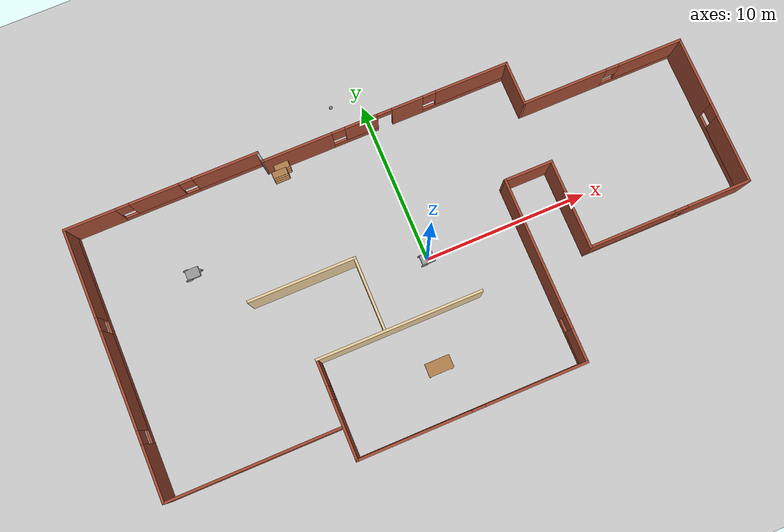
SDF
<sdf version="1.6">
 <world name="default">
  <plugin name="hellosam" filename="libhellosam.so"/>
  <light name="sun" type="directional">
   <pose>0 0 10 0 -0 0</pose>
   <diffuse>0.8 0.8 0.8 1</diffuse>
   <specular>0.2 0.2 0.2 1</specular>
   <attenuation>
    <range>1000</range>
    <constant>0.9</constant>
    <linear>0.01</linear>
    <quadratic>0.001</quadratic>
   </attenuation>
   <direction>-0.5 0.1 -0.9</direction>
   <spot><inner_angle>0</inner_angle><outer_angle>0</outer_angle><falloff>0</falloff></spot>
  </light>
  <model name="ground_plane">
   <static>1</static>
   <link name="link">
    <collision name="collision">
     <geometry><plane><normal>0 0 1</normal><size>100 100</size></plane></geometry>
     <surface><friction><ode><mu>100</mu><mu2>50</mu2></ode></friction></surface>
    </collision>
    <visual name="visual">
     <cast_shadows>0</cast_shadows>
     <geometry><plane><normal>0 0 1</normal><size>100 100</size></plane></geometry>
     <material>
      <script><uri>file://media/materials/scripts/gazebo.material</uri><name>Gazebo/Grey</name></script>
     </material>
    </visual>
   </link>
  </model>
  <gravity>0 0 -9.8</gravity>
  <magnetic_field>6e-06 2.3e-05 -4.2e-05</magnetic_field>
  <atmosphere type="adiabatic"/>
  <physics name="default_physics" default="0" type="ode">
   <max_step_size>0.001</max_step_size>
   <real_time_factor>1</real_time_factor>
   <real_time_update_rate>1000</real_time_update_rate>
  </physics>
  <scene><ambient>0.4 0.4 0.4 1</ambient><background>0.7 0.7 0.7 1</background><shadows>1</shadows></scene>
  <spherical_coordinates>
   <surface_model>EARTH_WGS84</surface_model>
   <latitude_deg>0</latitude_deg>
   <longitude_deg>0</longitude_deg>
   <elevation>0</elevation>
   <heading_deg>0</heading_deg>
  </spherical_coordinates>
  <model name="house2">
   <link name="Wall_33">
    <pose>0.928261 8.42543 0 0 -0 0</pose>
    <visual name="Wall_33_Visual_0">
     <pose>-5.47446 0 1.25 0 -0 0</pose>
     <geometry><box><size>4.30109 0.15 2.5</size></box></geometry>
     <material>
      <script><uri>file://media/materials/scripts/gazebo.material</uri><name>Gazebo/Bricks</name></script>
      <ambient>0.760784 0.662745 0.627451 1</ambient>
     </material>
     <meta><layer>0</layer></meta>
    </visual>
    <collision name="Wall_33_Collision_0">
     <geometry><box><size>4.30109 0.15 2.5</size></box></geometry>
     <pose>-5.47446 0 1.25 0 -0 0</pose>
    </collision>
    <visual name="Wall_33_Visual_1">
     <pose>1.34457 0 1.25 0 -0 0</pose>
     <geometry><box><size>1.93261 0.15 2.5</size></box></geometry>
     <material>
      <script><uri>file://media/materials/scripts/gazebo.material</uri><name>Gazebo/Bricks</name></script>
      <ambient>0.760784 0.662745 0.627451 1</ambient>
     </material>
     <meta><layer>0</layer></meta>
    </visual>
    <collision name="Wall_33_Collision_1">
     <geometry><box><size>1.93261 0.15 2.5</size></box></geometry>
     <pose>1.34457 0 1.25 0 -0 0</pose>
    </collision>
    <visual name="Wall_33_Visual_2">
     <pose>-1.92283 0 0.25 0 -0 0</pose>
     <geometry><box><size>2.80217 0.15 0.5</size></box></geometry>
     <material>
      <script><uri>file://media/materials/scripts/gazebo.material</uri><name>Gazebo/Bricks</name></script>
      <ambient>0.760784 0.662745 0.627451 1</ambient>
     </material>
     <meta><layer>0</layer></meta>
    </visual>
    <collision name="Wall_33_Collision_2">
     <geometry><box><size>2.80217 0.15 0.5</size></box></geometry>
     <pose>-1.92283 0 0.25 0 -0 0</pose>
    </collision>
    <visual name="Wall_33_Visual_3">
     <pose>4.96793 0 0.25 0 -0 0</pose>
     <geometry><box><size>5.31413 0.15 0.5</size></box></geometry>
     <material>
      <script><uri>file://media/materials/scripts/gazebo.material</uri><name>Gazebo/Bricks</name></script>
      <ambient>0.760784 0.662745 0.627451 1</ambient>
     </material>
     <meta><layer>0</layer></meta>
    </visual>
    <collision name="Wall_33_Collision_3">
     <geometry><box><size>5.31413 0.15 0.5</size></box></geometry>
     <pose>4.96793 0 0.25 0 -0 0</pose>
    </collision>
    <visual name="Wall_33_Visual_4">
     <pose>-1.52283 0 1.5 0 -0 0</pose>
     <geometry><box><size>2.00217 0.15 2</size></box></geometry>
     <material>
      <script><uri>file://media/materials/scripts/gazebo.material</uri><name>Gazebo/Bricks</name></script>
      <ambient>0.760784 0.662745 0.627451 1</ambient>
     </material>
     <meta><layer>0</layer></meta>
    </visual>
    <collision name="Wall_33_Collision_4">
     <geometry><box><size>2.00217 0.15 2</size></box></geometry>
     <pose>-1.52283 0 1.5 0 -0 0</pose>
    </collision>
    <visual name="Wall_33_Visual_5">
     <pose>-1.52283 0 1.5 0 -0 0</pose>
     <geometry><box><size>2.00217 0.15 2</size></box></geometry>
     <material>
      <script><uri>file://media/materials/scripts/gazebo.material</uri><name>Gazebo/Bricks</name></script>
      <ambient>0.760784 0.662745 0.627451 1</ambient>
     </material>
     <meta><layer>0</layer></meta>
    </visual>
    <collision name="Wall_33_Collision_5">
     <geometry><box><size>2.00217 0.15 2</size></box></geometry>
     <pose>-1.52283 0 1.5 0 -0 0</pose>
    </collision>
    <visual name="Wall_33_Visual_6">
     <pose>5.36794 0 1.5 0 -0 0</pose>
     <geometry><box><size>4.51413 0.15 2</size></box></geometry>
     <material>
      <script><uri>file://media/materials/scripts/gazebo.material</uri><name>Gazebo/Bricks</name></script>
      <ambient>0.760784 0.662745 0.627451 1</ambient>
     </material>
     <meta><layer>0</layer></meta>
    </visual>
    <collision name="Wall_33_Collision_6">
     <geometry><box><size>4.51413 0.15 2</size></box></geometry>
     <pose>5.36794 0 1.5 0 -0 0</pose>
    </collision>
    <visual name="Wall_33_Visual_7">
     <pose>-2.92391 0 1.9 0 -0 0</pose>
     <geometry><box><size>0.8 0.15 1.2</size></box></geometry>
     <material>
      <script><uri>file://media/materials/scripts/gazebo.material</uri><name>Gazebo/Bricks</name></script>
      <ambient>0.760784 0.662745 0.627451 1</ambient>
     </material>
     <meta><layer>0</layer></meta>
    </visual>
    <collision name="Wall_33_Collision_7">
     <geometry><box><size>0.8 0.15 1.2</size></box></geometry>
     <pose>-2.92391 0 1.9 0 -0 0</pose>
    </collision>
    <visual name="Wall_33_Visual_8">
     <pose>2.71087 0 1.9 0 -0 0</pose>
     <geometry><box><size>0.8 0.15 1.2</size></box></geometry>
     <material>
      <script><uri>file://media/materials/scripts/gazebo.material</uri><name>Gazebo/Bricks</name></script>
      <ambient>0.760784 0.662745 0.627451 1</ambient>
     </material>
     <meta><layer>0</layer></meta>
    </visual>
    <collision name="Wall_33_Collision_8">
     <geometry><box><size>0.8 0.15 1.2</size></box></geometry>
     <pose>2.71087 0 1.9 0 -0 0</pose>
    </collision>
    <visual name="Wall_33_Visual_9">
     <pose>-0.071739 0 2.25 0 -0 0</pose>
     <geometry><box><size>0.9 0.15 0.5</size></box></geometry>
     <material>
      <script><uri>file://media/materials/scripts/gazebo.material</uri><name>Gazebo/Bricks</name></script>
      <ambient>0.760784 0.662745 0.627451 1</ambient>
     </material>
     <meta><layer>0</layer></meta>
    </visual>
    <collision name="Wall_33_Collision_9">
     <geometry><box><size>0.9 0.15 0.5</size></box></geometry>
     <pose>-0.071739 0 2.25 0 -0 0</pose>
    </collision>
    <visual name="Wall_33_Visual_10">
     <pose>-0.071739 0 2.25 0 -0 0</pose>
     <geometry><box><size>0.9 0.15 0.5</size></box></geometry>
     <material>
      <script><uri>file://media/materials/scripts/gazebo.material</uri><name>Gazebo/Bricks</name></script>
      <ambient>0.760784 0.662745 0.627451 1</ambient>
     </material>
     <meta><layer>0</layer></meta>
    </visual>
    <collision name="Wall_33_Collision_10">
     <geometry><box><size>0.9 0.15 0.5</size></box></geometry>
     <pose>-0.071739 0 2.25 0 -0 0</pose>
    </collision>
   </link>
   <link name="Wall_34">
    <collision name="Wall_34_Collision">
     <geometry><box><size>2.75 0.15 2.5</size></box></geometry>
     <pose>0 0 1.25 0 -0 0</pose>
    </collision>
    <visual name="Wall_34_Visual">
     <pose>0 0 1.25 0 -0 0</pose>
     <geometry><box><size>2.75 0.15 2.5</size></box></geometry>
     <material>
      <script><uri>file://media/materials/scripts/gazebo.material</uri><name>Gazebo/Bricks</name></script>
      <ambient>1 1 1 1</ambient>
     </material>
     <meta><layer>0</layer></meta>
    </visual>
    <pose>8.47826 7.12543 0 0 0 -1.5708</pose>
   </link>
   <link name="Wall_35">
    <pose>13.4033 5.82543 0 0 -0 0</pose>
    <visual name="Wall_35_Visual_0">
     <pose>-2.38206 0 1.25 0 -0 0</pose>
     <geometry><box><size>5.23587 0.15 2.5</size></box></geometry>
     <material>
      <script><uri>file://media/materials/scripts/gazebo.material</uri><name>Gazebo/Bricks</name></script>
      <ambient>0.760784 0.662745 0.627451 1</ambient>
     </material>
     <meta><layer>0</layer></meta>
    </visual>
    <collision name="Wall_35_Collision_0">
     <geometry><box><size>5.23587 0.15 2.5</size></box></geometry>
     <pose>-2.38206 0 1.25 0 -0 0</pose>
    </collision>
    <visual name="Wall_35_Visual_1">
     <pose>2.61794 0 0.25 0 -0 0</pose>
     <geometry><box><size>4.76413 0.15 0.5</size></box></geometry>
     <material>
      <script><uri>file://media/materials/scripts/gazebo.material</uri><name>Gazebo/Bricks</name></script>
      <ambient>0.760784 0.662745 0.627451 1</ambient>
     </material>
     <meta><layer>0</layer></meta>
    </visual>
    <collision name="Wall_35_Collision_1">
     <geometry><box><size>4.76413 0.15 0.5</size></box></geometry>
     <pose>2.61794 0 0.25 0 -0 0</pose>
    </collision>
    <visual name="Wall_35_Visual_2">
     <pose>3.01794 0 1.5 0 -0 0</pose>
     <geometry><box><size>3.96413 0.15 2</size></box></geometry>
     <material>
      <script><uri>file://media/materials/scripts/gazebo.material</uri><name>Gazebo/Bricks</name></script>
      <ambient>0.760784 0.662745 0.627451 1</ambient>
     </material>
     <meta><layer>0</layer></meta>
    </visual>
    <collision name="Wall_35_Collision_2">
     <geometry><box><size>3.96413 0.15 2</size></box></geometry>
     <pose>3.01794 0 1.5 0 -0 0</pose>
    </collision>
    <visual name="Wall_35_Visual_3">
     <pose>0.63587 0 1.9 0 -0 0</pose>
     <geometry><box><size>0.8 0.15 1.2</size></box></geometry>
     <material>
      <script><uri>file://media/materials/scripts/gazebo.material</uri><name>Gazebo/Bricks</name></script>
      <ambient>0.760784 0.662745 0.627451 1</ambient>
     </material>
     <meta><layer>0</layer></meta>
    </visual>
    <collision name="Wall_35_Collision_3">
     <geometry><box><size>0.8 0.15 1.2</size></box></geometry>
     <pose>0.63587 0 1.9 0 -0 0</pose>
    </collision>
   </link>
   <link name="Wall_36">
    <pose>18.3283 1.27543 0 0 0 -1.5708</pose>
    <visual name="Wall_36_Visual_0">
     <pose>-2.4875 0 1.25 0 -0 0</pose>
     <geometry><box><size>4.275 0.15 2.5</size></box></geometry>
     <material>
      <script><uri>file://media/materials/scripts/gazebo.material</uri><name>Gazebo/Bricks</name></script>
      <ambient>0.760784 0.662745 0.627451 1</ambient>
     </material>
     <meta><layer>0</layer></meta>
    </visual>
    <collision name="Wall_36_Collision_0">
     <geometry><box><size>4.275 0.15 2.5</size></box></geometry>
     <pose>-2.4875 0 1.25 0 -0 0</pose>
    </collision>
    <visual name="Wall_36_Visual_1">
     <pose>2.1375 0 0.25 0 -0 0</pose>
     <geometry><box><size>4.975 0.15 0.5</size></box></geometry>
     <material>
      <script><uri>file://media/materials/scripts/gazebo.material</uri><name>Gazebo/Bricks</name></script>
      <ambient>0.760784 0.662745 0.627451 1</ambient>
     </material>
     <meta><layer>0</layer></meta>
    </visual>
    <collision name="Wall_36_Collision_1">
     <geometry><box><size>4.975 0.15 0.5</size></box></geometry>
     <pose>2.1375 0 0.25 0 -0 0</pose>
    </collision>
    <visual name="Wall_36_Visual_2">
     <pose>2.5375 0 1.5 0 -0 0</pose>
     <geometry><box><size>4.175 0.15 2</size></box></geometry>
     <material>
      <script><uri>file://media/materials/scripts/gazebo.material</uri><name>Gazebo/Bricks</name></script>
      <ambient>0.760784 0.662745 0.627451 1</ambient>
     </material>
     <meta><layer>0</layer></meta>
    </visual>
    <collision name="Wall_36_Collision_2">
     <geometry><box><size>4.175 0.15 2</size></box></geometry>
     <pose>2.5375 0 1.5 0 -0 0</pose>
    </collision>
    <visual name="Wall_36_Visual_3">
     <pose>0.049999 0 1.9 0 -0 0</pose>
     <geometry><box><size>0.8 0.15 1.2</size></box></geometry>
     <material>
      <script><uri>file://media/materials/scripts/gazebo.material</uri><name>Gazebo/Bricks</name></script>
      <ambient>0.760784 0.662745 0.627451 1</ambient>
     </material>
     <meta><layer>0</layer></meta>
    </visual>
    <collision name="Wall_36_Collision_3">
     <geometry><box><size>0.8 0.15 1.2</size></box></geometry>
     <pose>0.049999 0 1.9 0 -0 0</pose>
    </collision>
   </link>
   <link name="Wall_37">
    <pose>13.4033 -3.27457 0 0 -0 3.14159</pose>
    <visual name="Wall_37_Visual_0">
     <pose>-3.03533 0 1.25 0 -0 0</pose>
     <geometry><box><size>3.92935 0.15 2.5</size></box></geometry>
     <material>
      <script><uri>file://media/materials/scripts/gazebo.material</uri><name>Gazebo/Bricks</name></script>
      <ambient>0.760784 0.662745 0.627451 1</ambient>
     </material>
     <meta><layer>0</layer></meta>
    </visual>
    <collision name="Wall_37_Collision_0">
     <geometry><box><size>3.92935 0.15 2.5</size></box></geometry>
     <pose>-3.03533 0 1.25 0 -0 0</pose>
    </collision>
    <visual name="Wall_37_Visual_1">
     <pose>1.96467 0 0.25 0 -0 0</pose>
     <geometry><box><size>6.07065 0.15 0.5</size></box></geometry>
     <material>
      <script><uri>file://media/materials/scripts/gazebo.material</uri><name>Gazebo/Bricks</name></script>
      <ambient>0.760784 0.662745 0.627451 1</ambient>
     </material>
     <meta><layer>0</layer></meta>
    </visual>
    <collision name="Wall_37_Collision_1">
     <geometry><box><size>6.07065 0.15 0.5</size></box></geometry>
     <pose>1.96467 0 0.25 0 -0 0</pose>
    </collision>
    <visual name="Wall_37_Visual_2">
     <pose>2.36467 0 1.5 0 -0 0</pose>
     <geometry><box><size>5.27065 0.15 2</size></box></geometry>
     <material>
      <script><uri>file://media/materials/scripts/gazebo.material</uri><name>Gazebo/Bricks</name></script>
      <ambient>0.760784 0.662745 0.627451 1</ambient>
     </material>
     <meta><layer>0</layer></meta>
    </visual>
    <collision name="Wall_37_Collision_2">
     <geometry><box><size>5.27065 0.15 2</size></box></geometry>
     <pose>2.36467 0 1.5 0 -0 0</pose>
    </collision>
    <visual name="Wall_37_Visual_3">
     <pose>-0.670652 0 1.9 0 -0 0</pose>
     <geometry><box><size>0.8 0.15 1.2</size></box></geometry>
     <material>
      <script><uri>file://media/materials/scripts/gazebo.material</uri><name>Gazebo/Bricks</name></script>
      <ambient>0.760784 0.662745 0.627451 1</ambient>
     </material>
     <meta><layer>0</layer></meta>
    </visual>
    <collision name="Wall_37_Collision_3">
     <geometry><box><size>0.8 0.15 1.2</size></box></geometry>
     <pose>-0.670652 0 1.9 0 -0 0</pose>
    </collision>
   </link>
   <link name="Wall_38">
    <collision name="Wall_38_Collision">
     <geometry><box><size>5.5 0.15 2.5</size></box></geometry>
     <pose>0 0 1.25 0 -0 0</pose>
    </collision>
    <visual name="Wall_38_Visual">
     <pose>0 0 1.25 0 -0 0</pose>
     <geometry><box><size>5.5 0.15 2.5</size></box></geometry>
     <material>
      <script><uri>file://media/materials/scripts/gazebo.material</uri><name>Gazebo/Bricks</name></script>
      <ambient>1 1 1 1</ambient>
     </material>
     <meta><layer>0</layer></meta>
    </visual>
    <pose>8.47826 -0.599571 0 0 -0 1.5708</pose>
   </link>
   <link name="Wall_39">
    <collision name="Wall_39_Collision">
     <geometry><box><size>3 0.15 2.5</size></box></geometry>
     <pose>0 0 1.25 0 -0 0</pose>
    </collision>
    <visual name="Wall_39_Visual">
     <pose>0 0 1.25 0 -0 0</pose>
     <geometry><box><size>3 0.15 2.5</size></box></geometry>
     <material>
      <script><uri>file://media/materials/scripts/gazebo.material</uri><name>Gazebo/Bricks</name></script>
      <ambient>0.921569 0.807843 0.615686 1</ambient>
     </material>
     <meta><layer>0</layer></meta>
    </visual>
    <pose>7.05326 2.07543 0 0 -0 3.14159</pose>
   </link>
   <link name="Wall_40">
    <pose>5.62826 -3.47457 0 0 0 -1.5708</pose>
    <visual name="Wall_40_Visual_0">
     <pose>-1.43206 0 1.25 0 -0 0</pose>
     <geometry><box><size>8.38587 0.15 2.5</size></box></geometry>
     <material>
      <script><uri>file://media/materials/scripts/gazebo.material</uri><name>Gazebo/Bricks</name></script>
      <ambient>0.760784 0.662745 0.627451 1</ambient>
     </material>
     <meta><layer>0</layer></meta>
    </visual>
    <collision name="Wall_40_Collision_0">
     <geometry><box><size>8.38587 0.15 2.5</size></box></geometry>
     <pose>-1.43206 0 1.25 0 -0 0</pose>
    </collision>
    <visual name="Wall_40_Visual_1">
     <pose>4.19294 0 0.25 0 -0 0</pose>
     <geometry><box><size>2.86413 0.15 0.5</size></box></geometry>
     <material>
      <script><uri>file://media/materials/scripts/gazebo.material</uri><name>Gazebo/Bricks</name></script>
      <ambient>0.760784 0.662745 0.627451 1</ambient>
     </material>
     <meta><layer>0</layer></meta>
    </visual>
    <collision name="Wall_40_Collision_1">
     <geometry><box><size>2.86413 0.15 0.5</size></box></geometry>
     <pose>4.19294 0 0.25 0 -0 0</pose>
    </collision>
    <visual name="Wall_40_Visual_2">
     <pose>4.59293 0 1.5 0 -0 0</pose>
     <geometry><box><size>2.06413 0.15 2</size></box></geometry>
     <material>
      <script><uri>file://media/materials/scripts/gazebo.material</uri><name>Gazebo/Bricks</name></script>
      <ambient>0.760784 0.662745 0.627451 1</ambient>
     </material>
     <meta><layer>0</layer></meta>
    </visual>
    <collision name="Wall_40_Collision_2">
     <geometry><box><size>2.06413 0.15 2</size></box></geometry>
     <pose>4.59293 0 1.5 0 -0 0</pose>
    </collision>
    <visual name="Wall_40_Visual_3">
     <pose>3.16087 0 1.9 0 -0 0</pose>
     <geometry><box><size>0.8 0.15 1.2</size></box></geometry>
     <material>
      <script><uri>file://media/materials/scripts/gazebo.material</uri><name>Gazebo/Bricks</name></script>
      <ambient>0.760784 0.662745 0.627451 1</ambient>
     </material>
     <meta><layer>0</layer></meta>
    </visual>
    <collision name="Wall_40_Collision_3">
     <geometry><box><size>0.8 0.15 1.2</size></box></geometry>
     <pose>3.16087 0 1.9 0 -0 0</pose>
    </collision>
   </link>
   <link name="Wall_41">
    <pose>-1.17174 -9.02457 0 0 -0 3.14159</pose>
    <visual name="Wall_41_Visual_0">
     <pose>-3.79946 0 1.25 0 -0 0</pose>
     <geometry><box><size>6.15109 0.15 2.5</size></box></geometry>
     <material>
      <script><uri>file://media/materials/scripts/gazebo.material</uri><name>Gazebo/Bricks</name></script>
      <ambient>0.760784 0.662745 0.627451 1</ambient>
     </material>
     <meta><layer>0</layer></meta>
    </visual>
    <collision name="Wall_41_Collision_0">
     <geometry><box><size>6.15109 0.15 2.5</size></box></geometry>
     <pose>-3.79946 0 1.25 0 -0 0</pose>
    </collision>
    <visual name="Wall_41_Visual_1">
     <pose>3.07554 0 0.25 0 -0 0</pose>
     <geometry><box><size>7.59891 0.15 0.5</size></box></geometry>
     <material>
      <script><uri>file://media/materials/scripts/gazebo.material</uri><name>Gazebo/Bricks</name></script>
      <ambient>0.760784 0.662745 0.627451 1</ambient>
     </material>
     <meta><layer>0</layer></meta>
    </visual>
    <collision name="Wall_41_Collision_1">
     <geometry><box><size>7.59891 0.15 0.5</size></box></geometry>
     <pose>3.07554 0 0.25 0 -0 0</pose>
    </collision>
    <visual name="Wall_41_Visual_2">
     <pose>3.47554 0 1.5 0 -0 0</pose>
     <geometry><box><size>6.79891 0.15 2</size></box></geometry>
     <material>
      <script><uri>file://media/materials/scripts/gazebo.material</uri><name>Gazebo/Bricks</name></script>
      <ambient>0.760784 0.662745 0.627451 1</ambient>
     </material>
     <meta><layer>0</layer></meta>
    </visual>
    <collision name="Wall_41_Collision_2">
     <geometry><box><size>6.79891 0.15 2</size></box></geometry>
     <pose>3.47554 0 1.5 0 -0 0</pose>
    </collision>
    <visual name="Wall_41_Visual_3">
     <pose>-0.323913 0 1.9 0 -0 0</pose>
     <geometry><box><size>0.8 0.15 1.2</size></box></geometry>
     <material>
      <script><uri>file://media/materials/scripts/gazebo.material</uri><name>Gazebo/Bricks</name></script>
      <ambient>0.760784 0.662745 0.627451 1</ambient>
     </material>
     <meta><layer>0</layer></meta>
    </visual>
    <collision name="Wall_41_Collision_3">
     <geometry><box><size>0.8 0.15 1.2</size></box></geometry>
     <pose>-0.323913 0 1.9 0 -0 0</pose>
    </collision>
   </link>
   <link name="Wall_42">
    <pose>-7.97174 -6.09957 0 0 -0 1.5708</pose>
    <visual name="Wall_42_Visual_0">
     <pose>-1.20272 0 1.25 0 -0 0</pose>
     <geometry><box><size>3.59456 0.15 2.5</size></box></geometry>
     <material>
      <script><uri>file://media/materials/scripts/gazebo.material</uri><name>Gazebo/Bricks</name></script>
      <ambient>0.921569 0.807843 0.615686 1</ambient>
     </material>
     <meta><layer>0</layer></meta>
    </visual>
    <collision name="Wall_42_Collision_0">
     <geometry><box><size>3.59456 0.15 2.5</size></box></geometry>
     <pose>-1.20272 0 1.25 0 -0 0</pose>
    </collision>
    <visual name="Wall_42_Visual_1">
     <pose>1.79728 0 0.25 0 -0 0</pose>
     <geometry><box><size>2.40544 0.15 0.5</size></box></geometry>
     <material>
      <script><uri>file://media/materials/scripts/gazebo.material</uri><name>Gazebo/Bricks</name></script>
      <ambient>0.921569 0.807843 0.615686 1</ambient>
     </material>
     <meta><layer>0</layer></meta>
    </visual>
    <collision name="Wall_42_Collision_1">
     <geometry><box><size>2.40544 0.15 0.5</size></box></geometry>
     <pose>1.79728 0 0.25 0 -0 0</pose>
    </collision>
    <visual name="Wall_42_Visual_2">
     <pose>2.19728 0 1.5 0 -0 0</pose>
     <geometry><box><size>1.60544 0.15 2</size></box></geometry>
     <material>
      <script><uri>file://media/materials/scripts/gazebo.material</uri><name>Gazebo/Bricks</name></script>
      <ambient>0.921569 0.807843 0.615686 1</ambient>
     </material>
     <meta><layer>0</layer></meta>
    </visual>
    <collision name="Wall_42_Collision_2">
     <geometry><box><size>1.60544 0.15 2</size></box></geometry>
     <pose>2.19728 0 1.5 0 -0 0</pose>
    </collision>
    <visual name="Wall_42_Visual_3">
     <pose>0.994564 0 1.9 0 -0 0</pose>
     <geometry><box><size>0.8 0.15 1.2</size></box></geometry>
     <material>
      <script><uri>file://media/materials/scripts/gazebo.material</uri><name>Gazebo/Bricks</name></script>
      <ambient>0.921569 0.807843 0.615686 1</ambient>
     </material>
     <meta><layer>0</layer></meta>
    </visual>
    <collision name="Wall_42_Collision_3">
     <geometry><box><size>0.8 0.15 1.2</size></box></geometry>
     <pose>0.994564 0 1.9 0 -0 0</pose>
    </collision>
   </link>
   <link name="Wall_43">
    <collision name="Wall_43_Collision">
     <geometry><box><size>10 0.15 2.5</size></box></geometry>
     <pose>0 0 1.25 0 -0 0</pose>
    </collision>
    <visual name="Wall_43_Visual">
     <pose>0 0 1.25 0 -0 0</pose>
     <geometry><box><size>10 0.15 2.5</size></box></geometry>
     <material>
      <script><uri>file://media/materials/scripts/gazebo.material</uri><name>Gazebo/Grey</name></script>
      <ambient>0.921569 0.807843 0.615686 1</ambient>
     </material>
     <meta><layer>0</layer></meta>
    </visual>
    <pose>-3.04674 -3.17457 0 0 -0 0</pose>
   </link>
   <link name="Wall_45">
    <collision name="Wall_45_Collision">
     <geometry><box><size>4.5 0.15 2.5</size></box></geometry>
     <pose>0 0 1.25 0 -0 0</pose>
    </collision>
    <visual name="Wall_45_Visual">
     <pose>0 0 1.25 0 -0 0</pose>
     <geometry><box><size>4.5 0.15 2.5</size></box></geometry>
     <material>
      <script><uri>file://media/materials/scripts/gazebo.material</uri><name>Gazebo/Grey</name></script>
      <ambient>0.921569 0.807843 0.615686 1</ambient>
     </material>
     <meta><layer>0</layer></meta>
    </visual>
    <pose>-3.9087 -0.912614 0 0 -0 1.5708</pose>
   </link>
   <link name="Wall_46">
    <collision name="Wall_46_Collision">
     <geometry><box><size>6.5 0.15 2.5</size></box></geometry>
     <pose>0 0 1.25 0 -0 0</pose>
    </collision>
    <visual name="Wall_46_Visual">
     <pose>0 0 1.25 0 -0 0</pose>
     <geometry><box><size>6.5 0.15 2.5</size></box></geometry>
     <material>
      <script><uri>file://media/materials/scripts/gazebo.material</uri><name>Gazebo/Grey</name></script>
      <ambient>0.921569 0.807843 0.615686 1</ambient>
     </material>
     <meta><layer>0</layer></meta>
    </visual>
    <pose>-7.0837 1.26239 0 0 -0 3.14159</pose>
   </link>
   <link name="Wall_48">
    <collision name="Wall_48_Collision">
     <geometry><box><size>10.5 0.15 2.5</size></box></geometry>
     <pose>0 0 1.25 0 -0 0</pose>
    </collision>
    <visual name="Wall_48_Visual">
     <pose>0 0 1.25 0 -0 0</pose>
     <geometry><box><size>10.5 0.15 2.5</size></box></geometry>
     <material>
      <script><uri>file://media/materials/scripts/gazebo.material</uri><name>Gazebo/Bricks</name></script>
      <ambient>0.760784 0.662745 0.627451 1</ambient>
     </material>
     <meta><layer>0</layer></meta>
    </visual>
    <pose>-13.1533 -7.08762 0 0 -0 3.14159</pose>
   </link>
   <link name="Wall_49">
    <pose>-18.3283 0.962386 0 0 -0 1.5708</pose>
    <visual name="Wall_49_Visual_0">
     <pose>-6.42663 0 1.25 0 -0 0</pose>
     <geometry><box><size>3.39674 0.15 2.5</size></box></geometry>
     <material>
      <script><uri>file://media/materials/scripts/gazebo.material</uri><name>Gazebo/Bricks</name></script>
      <ambient>0.760784 0.662745 0.627451 1</ambient>
     </material>
     <meta><layer>0</layer></meta>
    </visual>
    <collision name="Wall_49_Collision_0">
     <geometry><box><size>3.39674 0.15 2.5</size></box></geometry>
     <pose>-6.42663 0 1.25 0 -0 0</pose>
    </collision>
    <visual name="Wall_49_Visual_1">
     <pose>1.69837 0 0.25 0 -0 0</pose>
     <geometry><box><size>12.8533 0.15 0.5</size></box></geometry>
     <material>
      <script><uri>file://media/materials/scripts/gazebo.material</uri><name>Gazebo/Bricks</name></script>
      <ambient>0.760784 0.662745 0.627451 1</ambient>
     </material>
     <meta><layer>0</layer></meta>
    </visual>
    <collision name="Wall_49_Collision_1">
     <geometry><box><size>12.8533 0.15 0.5</size></box></geometry>
     <pose>1.69837 0 0.25 0 -0 0</pose>
    </collision>
    <visual name="Wall_49_Visual_2">
     <pose>-1.00652 0 1.5 0 -0 0</pose>
     <geometry><box><size>5.84348 0.15 2</size></box></geometry>
     <material>
      <script><uri>file://media/materials/scripts/gazebo.material</uri><name>Gazebo/Bricks</name></script>
      <ambient>0.760784 0.662745 0.627451 1</ambient>
     </material>
     <meta><layer>0</layer></meta>
    </visual>
    <collision name="Wall_49_Collision_2">
     <geometry><box><size>5.84348 0.15 2</size></box></geometry>
     <pose>-1.00652 0 1.5 0 -0 0</pose>
    </collision>
    <visual name="Wall_49_Visual_3">
     <pose>5.42011 0 1.5 0 -0 0</pose>
     <geometry><box><size>5.40978 0.15 2</size></box></geometry>
     <material>
      <script><uri>file://media/materials/scripts/gazebo.material</uri><name>Gazebo/Bricks</name></script>
      <ambient>0.760784 0.662745 0.627451 1</ambient>
     </material>
     <meta><layer>0</layer></meta>
    </visual>
    <collision name="Wall_49_Collision_3">
     <geometry><box><size>5.40978 0.15 2</size></box></geometry>
     <pose>5.42011 0 1.5 0 -0 0</pose>
    </collision>
    <visual name="Wall_49_Visual_4">
     <pose>-4.32826 0 1.9 0 -0 0</pose>
     <geometry><box><size>0.8 0.15 1.2</size></box></geometry>
     <material>
      <script><uri>file://media/materials/scripts/gazebo.material</uri><name>Gazebo/Bricks</name></script>
      <ambient>0.760784 0.662745 0.627451 1</ambient>
     </material>
     <meta><layer>0</layer></meta>
    </visual>
    <collision name="Wall_49_Collision_4">
     <geometry><box><size>0.8 0.15 1.2</size></box></geometry>
     <pose>-4.32826 0 1.9 0 -0 0</pose>
    </collision>
    <visual name="Wall_49_Visual_5">
     <pose>2.31522 0 1.9 0 -0 0</pose>
     <geometry><box><size>0.8 0.15 1.2</size></box></geometry>
     <material>
      <script><uri>file://media/materials/scripts/gazebo.material</uri><name>Gazebo/Bricks</name></script>
      <ambient>0.760784 0.662745 0.627451 1</ambient>
     </material>
     <meta><layer>0</layer></meta>
    </visual>
    <collision name="Wall_49_Collision_5">
     <geometry><box><size>0.8 0.15 1.2</size></box></geometry>
     <pose>2.31522 0 1.9 0 -0 0</pose>
    </collision>
   </link>
   <link name="Wall_50">
    <pose>-12.5283 9.01239 0 0 -0 0</pose>
    <visual name="Wall_50_Visual_0">
     <pose>-4.30598 0 1.25 0 -0 0</pose>
     <geometry><box><size>3.13804 0.15 2.5</size></box></geometry>
     <material>
      <script><uri>file://media/materials/scripts/gazebo.material</uri><name>Gazebo/Bricks</name></script>
      <ambient>1 1 1 1</ambient>
     </material>
     <meta><layer>0</layer></meta>
    </visual>
    <collision name="Wall_50_Collision_0">
     <geometry><box><size>3.13804 0.15 2.5</size></box></geometry>
     <pose>-4.30598 0 1.25 0 -0 0</pose>
    </collision>
    <visual name="Wall_50_Visual_1">
     <pose>1.56902 0 0.25 0 -0 0</pose>
     <geometry><box><size>8.61196 0.15 0.5</size></box></geometry>
     <material>
      <script><uri>file://media/materials/scripts/gazebo.material</uri><name>Gazebo/Bricks</name></script>
      <ambient>1 1 1 1</ambient>
     </material>
     <meta><layer>0</layer></meta>
    </visual>
    <collision name="Wall_50_Collision_1">
     <geometry><box><size>8.61196 0.15 0.5</size></box></geometry>
     <pose>1.56902 0 0.25 0 -0 0</pose>
    </collision>
    <visual name="Wall_50_Visual_2">
     <pose>-0.441305 0 1.5 0 -0 0</pose>
     <geometry><box><size>2.99131 0.15 2</size></box></geometry>
     <material>
      <script><uri>file://media/materials/scripts/gazebo.material</uri><name>Gazebo/Bricks</name></script>
      <ambient>1 1 1 1</ambient>
     </material>
     <meta><layer>0</layer></meta>
    </visual>
    <collision name="Wall_50_Collision_2">
     <geometry><box><size>2.99131 0.15 2</size></box></geometry>
     <pose>-0.441305 0 1.5 0 -0 0</pose>
    </collision>
    <visual name="Wall_50_Visual_3">
     <pose>3.86467 0 1.5 0 -0 0</pose>
     <geometry><box><size>4.02065 0.15 2</size></box></geometry>
     <material>
      <script><uri>file://media/materials/scripts/gazebo.material</uri><name>Gazebo/Bricks</name></script>
      <ambient>1 1 1 1</ambient>
     </material>
     <meta><layer>0</layer></meta>
    </visual>
    <collision name="Wall_50_Collision_3">
     <geometry><box><size>4.02065 0.15 2</size></box></geometry>
     <pose>3.86467 0 1.5 0 -0 0</pose>
    </collision>
    <visual name="Wall_50_Visual_4">
     <pose>-2.33696 0 1.9 0 -0 0</pose>
     <geometry><box><size>0.8 0.15 1.2</size></box></geometry>
     <material>
      <script><uri>file://media/materials/scripts/gazebo.material</uri><name>Gazebo/Bricks</name></script>
      <ambient>1 1 1 1</ambient>
     </material>
     <meta><layer>0</layer></meta>
    </visual>
    <collision name="Wall_50_Collision_4">
     <geometry><box><size>0.8 0.15 1.2</size></box></geometry>
     <pose>-2.33696 0 1.9 0 -0 0</pose>
    </collision>
    <visual name="Wall_50_Visual_5">
     <pose>1.45435 0 1.9 0 -0 0</pose>
     <geometry><box><size>0.8 0.15 1.2</size></box></geometry>
     <material>
      <script><uri>file://media/materials/scripts/gazebo.material</uri><name>Gazebo/Bricks</name></script>
      <ambient>1 1 1 1</ambient>
     </material>
     <meta><layer>0</layer></meta>
    </visual>
    <collision name="Wall_50_Collision_5">
     <geometry><box><size>0.8 0.15 1.2</size></box></geometry>
     <pose>1.45435 0 1.9 0 -0 0</pose>
    </collision>
   </link>
   <link name="Wall_51">
    <collision name="Wall_51_Collision">
     <geometry><box><size>0.746544 0.15 2.5</size></box></geometry>
     <pose>0 0 1.25 0 -0 0</pose>
    </collision>
    <visual name="Wall_51_Visual">
     <pose>0 0 1.25 0 -0 0</pose>
     <geometry><box><size>0.746544 0.15 2.5</size></box></geometry>
     <material>
      <script><uri>file://media/materials/scripts/gazebo.material</uri><name>Gazebo/Grey</name></script>
      <ambient>1 1 1 1</ambient>
     </material>
     <meta><layer>0</layer></meta>
    </visual>
    <pose>-6.675 8.71891 0 0 0 -1.39127</pose>
   </link>
   <static>1</static>
  </model>
  <model name="table">
   <static>1</static>
   <link name="link">
    <collision name="surface">
     <pose>0 0 1 0 -0 0</pose>
     <geometry><box><size>1.5 0.8 0.03</size></box></geometry>
     <surface><friction><ode><mu>0.6</mu><mu2>0.6</mu2></ode></friction></surface>
    </collision>
    <visual name="visual1">
     <pose>0 0 1 0 -0 0</pose>
     <geometry><box><size>1.5 0.8 0.03</size></box></geometry>
     <material>
      <script><uri>file://media/materials/scripts/gazebo.material</uri><name>Gazebo/Wood</name></script>
     </material>
    </visual>
    <collision name="front_left_leg">
     <pose>0.68 0.38 0.5 0 -0 0</pose>
     <geometry><cylinder><radius>0.02</radius><length>1</length></cylinder></geometry>
    </collision>
    <visual name="front_left_leg">
     <pose>0.68 0.38 0.5 0 -0 0</pose>
     <geometry><cylinder><radius>0.02</radius><length>1</length></cylinder></geometry>
     <material>
      <script><uri>file://media/materials/scripts/gazebo.material</uri><name>Gazebo/Grey</name></script>
     </material>
    </visual>
    <collision name="front_right_leg">
     <pose>0.68 -0.38 0.5 0 -0 0</pose>
     <geometry><cylinder><radius>0.02</radius><length>1</length></cylinder></geometry>
    </collision>
    <visual name="front_right_leg">
     <pose>0.68 -0.38 0.5 0 -0 0</pose>
     <geometry><cylinder><radius>0.02</radius><length>1</length></cylinder></geometry>
     <material>
      <script><uri>file://media/materials/scripts/gazebo.material</uri><name>Gazebo/Grey</name></script>
     </material>
    </visual>
    <collision name="back_right_leg">
     <pose>-0.68 -0.38 0.5 0 -0 0</pose>
     <geometry><cylinder><radius>0.02</radius><length>1</length></cylinder></geometry>
    </collision>
    <visual name="back_right_leg">
     <pose>-0.68 -0.38 0.5 0 -0 0</pose>
     <geometry><cylinder><radius>0.02</radius><length>1</length></cylinder></geometry>
     <material>
      <script><uri>file://media/materials/scripts/gazebo.material</uri><name>Gazebo/Grey</name></script>
     </material>
    </visual>
    <collision name="back_left_leg">
     <pose>-0.68 0.38 0.5 0 -0 0</pose>
     <geometry><cylinder><radius>0.02</radius><length>1</length></cylinder></geometry>
    </collision>
    <visual name="back_left_leg">
     <pose>-0.68 0.38 0.5 0 -0 0</pose>
     <geometry><cylinder><radius>0.02</radius><length>1</length></cylinder></geometry>
     <material>
      <script><uri>file://media/materials/scripts/gazebo.material</uri><name>Gazebo/Grey</name></script>
     </material>
    </visual>
   </link>
   <pose>-1.83642 -6.01914 0 0 -0 0</pose>
  </model>
  <model name="bookshelf">
   <static>1</static>
   <link name="link">
    <inertial><mass>1</mass></inertial>
    <collision name="back">
     <pose>0 0.005 0.6 0 -0 0</pose>
     <geometry><box><size>0.9 0.01 1.2</size></box></geometry>
    </collision>
    <visual name="visual1">
     <pose>0 0.005 0.6 0 -0 0</pose>
     <geometry><box><size>0.9 0.01 1.2</size></box></geometry>
     <material>
      <script><uri>file://media/materials/scripts/gazebo.material</uri><name>Gazebo/Wood</name></script>
     </material>
    </visual>
    <collision name="left_side">
     <pose>0.45 -0.195 0.6 0 -0 0</pose>
     <geometry><box><size>0.02 0.4 1.2</size></box></geometry>
    </collision>
    <visual name="visual2">
     <pose>0.45 -0.195 0.6 0 -0 0</pose>
     <geometry><box><size>0.02 0.4 1.2</size></box></geometry>
     <material>
      <script><uri>file://media/materials/scripts/gazebo.material</uri><name>Gazebo/Wood</name></script>
     </material>
    </visual>
    <collision name="right_side">
     <pose>-0.45 -0.195 0.6 0 -0 0</pose>
     <geometry><box><size>0.02 0.4 1.2</size></box></geometry>
    </collision>
    <visual name="visual3">
     <pose>-0.45 -0.195 0.6 0 -0 0</pose>
     <geometry><box><size>0.02 0.4 1.2</size></box></geometry>
     <material>
      <script><uri>file://media/materials/scripts/gazebo.material</uri><name>Gazebo/Wood</name></script>
     </material>
    </visual>
    <collision name="bottom">
     <pose>0 -0.195 0.03 0 -0 0</pose>
     <geometry><box><size>0.88 0.4 0.06</size></box></geometry>
    </collision>
    <visual name="visual4">
     <pose>0 -0.195 0.03 0 -0 0</pose>
     <geometry><box><size>0.88 0.4 0.06</size></box></geometry>
     <material>
      <script><uri>file://media/materials/scripts/gazebo.material</uri><name>Gazebo/Wood</name></script>
     </material>
    </visual>
    <collision name="top">
     <pose>0 -0.195 1.19 0 -0 0</pose>
     <geometry><box><size>0.88 0.4 0.02</size></box></geometry>
    </collision>
    <visual name="visual5">
     <pose>0 -0.195 1.19 0 -0 0</pose>
     <geometry><box><size>0.88 0.4 0.02</size></box></geometry>
     <material>
      <script><uri>file://media/materials/scripts/gazebo.material</uri><name>Gazebo/Wood</name></script>
     </material>
    </visual>
    <collision name="low_shelf">
     <pose>0 -0.195 0.43 0 -0 0</pose>
     <geometry><box><size>0.88 0.4 0.02</size></box></geometry>
    </collision>
    <visual name="visual6">
     <pose>0 -0.195 0.43 0 -0 0</pose>
     <geometry><box><size>0.88 0.4 0.02</size></box></geometry>
     <material>
      <script><uri>file://media/materials/scripts/gazebo.material</uri><name>Gazebo/Wood</name></script>
     </material>
    </visual>
    <collision name="high_shelf">
     <pose>0 -0.195 0.8 0 -0 0</pose>
     <geometry><box><size>0.88 0.4 0.02</size></box></geometry>
    </collision>
    <visual name="visual7">
     <pose>0 -0.195 0.8 0 -0 0</pose>
     <geometry><box><size>0.88 0.4 0.02</size></box></geometry>
     <material>
      <script><uri>file://media/materials/scripts/gazebo.material</uri><name>Gazebo/Wood</name></script>
     </material>
    </visual>
   </link>
   <pose>-5.7523 8.34395 0 0 -0 0</pose>
  </model>
  <model name="bookshelf_0">
   <static>1</static>
   <link name="link">
    <inertial><mass>1</mass></inertial>
    <collision name="back">
     <pose>0 0.005 0.6 0 -0 0</pose>
     <geometry><box><size>0.9 0.01 1.2</size></box></geometry>
    </collision>
    <visual name="visual1">
     <pose>0 0.005 0.6 0 -0 0</pose>
     <geometry><box><size>0.9 0.01 1.2</size></box></geometry>
     <material>
      <script><uri>file://media/materials/scripts/gazebo.material</uri><name>Gazebo/Wood</name></script>
     </material>
    </visual>
    <collision name="left_side">
     <pose>0.45 -0.195 0.6 0 -0 0</pose>
     <geometry><box><size>0.02 0.4 1.2</size></box></geometry>
    </collision>
    <visual name="visual2">
     <pose>0.45 -0.195 0.6 0 -0 0</pose>
     <geometry><box><size>0.02 0.4 1.2</size></box></geometry>
     <material>
      <script><uri>file://media/materials/scripts/gazebo.material</uri><name>Gazebo/Wood</name></script>
     </material>
    </visual>
    <collision name="right_side">
     <pose>-0.45 -0.195 0.6 0 -0 0</pose>
     <geometry><box><size>0.02 0.4 1.2</size></box></geometry>
    </collision>
    <visual name="visual3">
     <pose>-0.45 -0.195 0.6 0 -0 0</pose>
     <geometry><box><size>0.02 0.4 1.2</size></box></geometry>
     <material>
      <script><uri>file://media/materials/scripts/gazebo.material</uri><name>Gazebo/Wood</name></script>
     </material>
    </visual>
    <collision name="bottom">
     <pose>0 -0.195 0.03 0 -0 0</pose>
     <geometry><box><size>0.88 0.4 0.06</size></box></geometry>
    </collision>
    <visual name="visual4">
     <pose>0 -0.195 0.03 0 -0 0</pose>
     <geometry><box><size>0.88 0.4 0.06</size></box></geometry>
     <material>
      <script><uri>file://media/materials/scripts/gazebo.material</uri><name>Gazebo/Wood</name></script>
     </material>
    </visual>
    <collision name="top">
     <pose>0 -0.195 1.19 0 -0 0</pose>
     <geometry><box><size>0.88 0.4 0.02</size></box></geometry>
    </collision>
    <visual name="visual5">
     <pose>0 -0.195 1.19 0 -0 0</pose>
     <geometry><box><size>0.88 0.4 0.02</size></box></geometry>
     <material>
      <script><uri>file://media/materials/scripts/gazebo.material</uri><name>Gazebo/Wood</name></script>
     </material>
    </visual>
    <collision name="low_shelf">
     <pose>0 -0.195 0.43 0 -0 0</pose>
     <geometry><box><size>0.88 0.4 0.02</size></box></geometry>
    </collision>
    <visual name="visual6">
     <pose>0 -0.195 0.43 0 -0 0</pose>
     <geometry><box><size>0.88 0.4 0.02</size></box></geometry>
     <material>
      <script><uri>file://media/materials/scripts/gazebo.material</uri><name>Gazebo/Wood</name></script>
     </material>
    </visual>
    <collision name="high_shelf">
     <pose>0 -0.195 0.8 0 -0 0</pose>
     <geometry><box><size>0.88 0.4 0.02</size></box></geometry>
    </collision>
    <visual name="visual7">
     <pose>0 -0.195 0.8 0 -0 0</pose>
     <geometry><box><size>0.88 0.4 0.02</size></box></geometry>
     <material>
      <script><uri>file://media/materials/scripts/gazebo.material</uri><name>Gazebo/Wood</name></script>
     </material>
    </visual>
   </link>
   <pose>-5.99911 8.00478 0 0 -0 0</pose>
  </model>
  <model name="mycart">
   <link name="link_1">
    <pose>-0.06 0 0.04 0 -0 0</pose>
    <inertial>
     <mass>1</mass>
     <inertia>
      <ixx>0.166667</ixx>
      <ixy>0</ixy>
      <ixz>0</ixz>
      <iyy>0.166667</iyy>
      <iyz>0</iyz>
      <izz>0.166667</izz>
     </inertia>
    </inertial>
    <visual name="visual">
     <geometry><box><size>0.8 0.6 0.2</size></box></geometry>
     <material>
      <lighting>1</lighting>
      <script><uri>file://media/materials/scripts/gazebo.material</uri><name>Gazebo/Grey</name></script>
      <shader type="pixel"><normal_map>__default__</normal_map></shader>
      <ambient>0.3 0.3 0.3 1</ambient>
      <diffuse>0.7 0.7 0.7 1</diffuse>
      <specular>0.01 0.01 0.01 1</specular>
      <emissive>0 0 0 1</emissive>
     </material>
    </visual>
    <collision name="collision">
     <geometry><box><size>0.8 0.6 0.2</size></box></geometry>
     <surface>
      <friction>
       <ode><mu>1</mu><mu2>1</mu2><fdir1>0 0 0</fdir1><slip1>0</slip1><slip2>0</slip2></ode>
       <torsional>
        <coefficient>1</coefficient>
        <patch_radius>0</patch_radius>
        <surface_radius>0</surface_radius>
        <use_patch_radius>1</use_patch_radius>
        <ode><slip>0</slip></ode>
       </torsional>
      </friction>
      <bounce><restitution_coefficient>0</restitution_coefficient><threshold>1e+06</threshold></bounce>
      <contact>
       <collide_without_contact>0</collide_without_contact>
       <collide_without_contact_bitmask>1</collide_without_contact_bitmask>
       <collide_bitmask>1</collide_bitmask>
       <ode>
        <soft_cfm>0</soft_cfm>
        <soft_erp>0.2</soft_erp>
        <kp>1e+13</kp>
        <kd>1</kd>
        <max_vel>0.01</max_vel>
        <min_depth>0</min_depth>
       </ode>
       <bullet>
        <split_impulse>1</split_impulse>
        <split_impulse_penetration_threshold>-0.01</split_impulse_penetration_threshold>
        <soft_cfm>0</soft_cfm>
        <soft_erp>0.2</soft_erp>
        <kp>1e+13</kp>
        <kd>1</kd>
       </bullet>
      </contact>
     </surface>
    </collision>
   </link>
   <link name="link_2">
    <pose>-0.36 0.3 -0.01 1.5707 -0 0</pose>
    <inertial>
     <mass>1</mass>
     <inertia><ixx>0.145833</ixx><ixy>0</ixy><ixz>0</ixz><iyy>0.145833</iyy><iyz>0</iyz><izz>0.125</izz></inertia>
    </inertial>
    <visual name="visual">
     <geometry><cylinder><radius>0.2</radius><length>0.05</length></cylinder></geometry>
     <material>
      <lighting>1</lighting>
      <script><uri>file://media/materials/scripts/gazebo.material</uri><name>Gazebo/Grey</name></script>
      <shader type="pixel"><normal_map>__default__</normal_map></shader>
      <ambient>0.3 0.3 0.3 1</ambient>
      <diffuse>0.7 0.7 0.7 1</diffuse>
      <specular>0.01 0.01 0.01 1</specular>
      <emissive>0 0 0 1</emissive>
     </material>
    </visual>
    <collision name="collision">
     <geometry><cylinder><radius>0.2</radius><length>0.05</length></cylinder></geometry>
     <surface>
      <friction>
       <ode><mu>1</mu><mu2>1</mu2><fdir1>0 0 0</fdir1><slip1>0</slip1><slip2>0</slip2></ode>
       <torsional>
        <coefficient>1</coefficient>
        <patch_radius>0</patch_radius>
        <surface_radius>0</surface_radius>
        <use_patch_radius>1</use_patch_radius>
        <ode><slip>0</slip></ode>
       </torsional>
      </friction>
      <bounce><restitution_coefficient>0</restitution_coefficient><threshold>1e+06</threshold></bounce>
      <contact>
       <collide_without_contact>0</collide_without_contact>
       <collide_without_contact_bitmask>1</collide_without_contact_bitmask>
       <collide_bitmask>1</collide_bitmask>
       <ode>
        <soft_cfm>0</soft_cfm>
        <soft_erp>0.2</soft_erp>
        <kp>1e+13</kp>
        <kd>1</kd>
        <max_vel>0.01</max_vel>
        <min_depth>0</min_depth>
       </ode>
       <bullet>
        <split_impulse>1</split_impulse>
        <split_impulse_penetration_threshold>-0.01</split_impulse_penetration_threshold>
        <soft_cfm>0</soft_cfm>
        <soft_erp>0.2</soft_erp>
        <kp>1e+13</kp>
        <kd>1</kd>
       </bullet>
      </contact>
     </surface>
    </collision>
   </link>
   <link name="link_2_clone">
    <pose>-0.36 -0.3 -0.01 1.5707 -0 0</pose>
    <inertial>
     <mass>1</mass>
     <inertia><ixx>0.145833</ixx><ixy>0</ixy><ixz>0</ixz><iyy>0.145833</iyy><iyz>0</iyz><izz>0.125</izz></inertia>
    </inertial>
    <visual name="visual">
     <geometry><cylinder><radius>0.2</radius><length>0.05</length></cylinder></geometry>
     <material>
      <lighting>1</lighting>
      <script><uri>file://media/materials/scripts/gazebo.material</uri><name>Gazebo/Grey</name></script>
      <shader type="pixel"><normal_map>__default__</normal_map></shader>
      <ambient>0.3 0.3 0.3 1</ambient>
      <diffuse>0.7 0.7 0.7 1</diffuse>
      <specular>0.01 0.01 0.01 1</specular>
      <emissive>0 0 0 1</emissive>
     </material>
    </visual>
    <collision name="collision">
     <geometry><cylinder><radius>0.2</radius><length>0.05</length></cylinder></geometry>
     <surface>
      <friction>
       <ode><mu>1</mu><mu2>1</mu2><fdir1>0 0 0</fdir1><slip1>0</slip1><slip2>0</slip2></ode>
       <torsional>
        <coefficient>1</coefficient>
        <patch_radius>0</patch_radius>
        <surface_radius>0</surface_radius>
        <use_patch_radius>1</use_patch_radius>
        <ode><slip>0</slip></ode>
       </torsional>
      </friction>
      <bounce><restitution_coefficient>0</restitution_coefficient><threshold>1e+06</threshold></bounce>
      <contact>
       <collide_without_contact>0</collide_without_contact>
       <collide_without_contact_bitmask>1</collide_without_contact_bitmask>
       <collide_bitmask>1</collide_bitmask>
       <ode>
        <soft_cfm>0</soft_cfm>
        <soft_erp>0.2</soft_erp>
        <kp>1e+13</kp>
        <kd>1</kd>
        <max_vel>0.01</max_vel>
        <min_depth>0</min_depth>
       </ode>
       <bullet>
        <split_impulse>1</split_impulse>
        <split_impulse_penetration_threshold>-0.01</split_impulse_penetration_threshold>
        <soft_cfm>0</soft_cfm>
        <soft_erp>0.2</soft_erp>
        <kp>1e+13</kp>
        <kd>1</kd>
       </bullet>
      </contact>
     </surface>
    </collision>
   </link>
   <link name="link_3">
    <pose>0.39 0 0.04 0 -0 0</pose>
    <inertial>
     <mass>1</mass>
     <inertia><ixx>0.145833</ixx><ixy>0</ixy><ixz>0</ixz><iyy>0.145833</iyy><iyz>0</iyz><izz>0.125</izz></inertia>
    </inertial>
    <visual name="visual">
     <geometry><cylinder><radius>0.1</radius><length>0.05</length></cylinder></geometry>
     <material>
      <lighting>1</lighting>
      <script><uri>file://media/materials/scripts/gazebo.material</uri><name>Gazebo/Grey</name></script>
      <shader type="pixel"><normal_map>__default__</normal_map></shader>
      <ambient>0.3 0.3 0.3 1</ambient>
      <diffuse>0.7 0.7 0.7 1</diffuse>
      <specular>0.01 0.01 0.01 1</specular>
      <emissive>0 0 0 1</emissive>
     </material>
    </visual>
    <collision name="collision">
     <geometry><cylinder><radius>0.1</radius><length>0.05</length></cylinder></geometry>
     <surface>
      <friction>
       <ode><mu>1</mu><mu2>1</mu2><fdir1>0 0 0</fdir1><slip1>0</slip1><slip2>0</slip2></ode>
       <torsional>
        <coefficient>1</coefficient>
        <patch_radius>0</patch_radius>
        <surface_radius>0</surface_radius>
        <use_patch_radius>1</use_patch_radius>
        <ode><slip>0</slip></ode>
       </torsional>
      </friction>
      <bounce><restitution_coefficient>0</restitution_coefficient><threshold>1e+06</threshold></bounce>
      <contact>
       <collide_without_contact>0</collide_without_contact>
       <collide_without_contact_bitmask>1</collide_without_contact_bitmask>
       <collide_bitmask>1</collide_bitmask>
       <ode>
        <soft_cfm>0</soft_cfm>
        <soft_erp>0.2</soft_erp>
        <kp>1e+13</kp>
        <kd>1</kd>
        <max_vel>0.01</max_vel>
        <min_depth>0</min_depth>
       </ode>
       <bullet>
        <split_impulse>1</split_impulse>
        <split_impulse_penetration_threshold>-0.01</split_impulse_penetration_threshold>
        <soft_cfm>0</soft_cfm>
        <soft_erp>0.2</soft_erp>
        <kp>1e+13</kp>
        <kd>1</kd>
       </bullet>
      </contact>
     </surface>
    </collision>
   </link>
   <link name="link_4">
    <pose>0.39 0 -0.06 1.5707 -0 0</pose>
    <inertial>
     <mass>1</mass>
     <inertia><ixx>0.145833</ixx><ixy>0</ixy><ixz>0</ixz><iyy>0.145833</iyy><iyz>0</iyz><izz>0.125</izz></inertia>
    </inertial>
    <visual name="visual">
     <geometry><cylinder><radius>0.15</radius><length>0.05</length></cylinder></geometry>
     <material>
      <lighting>1</lighting>
      <script><uri>file://media/materials/scripts/gazebo.material</uri><name>Gazebo/Grey</name></script>
      <shader type="pixel"><normal_map>__default__</normal_map></shader>
      <ambient>0.3 0.3 0.3 1</ambient>
      <diffuse>0.7 0.7 0.7 1</diffuse>
      <specular>0.01 0.01 0.01 1</specular>
      <emissive>0 0 0 1</emissive>
     </material>
    </visual>
    <collision name="collision">
     <geometry><cylinder><radius>0.15</radius><length>0.05</length></cylinder></geometry>
     <surface>
      <friction>
       <ode><mu>1</mu><mu2>1</mu2><fdir1>0 0 0</fdir1><slip1>0</slip1><slip2>0</slip2></ode>
       <torsional>
        <coefficient>1</coefficient>
        <patch_radius>0</patch_radius>
        <surface_radius>0</surface_radius>
        <use_patch_radius>1</use_patch_radius>
        <ode><slip>0</slip></ode>
       </torsional>
      </friction>
      <bounce><restitution_coefficient>0</restitution_coefficient><threshold>1e+06</threshold></bounce>
      <contact>
       <collide_without_contact>0</collide_without_contact>
       <collide_without_contact_bitmask>1</collide_without_contact_bitmask>
       <collide_bitmask>1</collide_bitmask>
       <ode>
        <soft_cfm>0</soft_cfm>
        <soft_erp>0.2</soft_erp>
        <kp>1e+13</kp>
        <kd>1</kd>
        <max_vel>0.01</max_vel>
        <min_depth>0</min_depth>
       </ode>
       <bullet>
        <split_impulse>1</split_impulse>
        <split_impulse_penetration_threshold>-0.01</split_impulse_penetration_threshold>
        <soft_cfm>0</soft_cfm>
        <soft_erp>0.2</soft_erp>
        <kp>1e+13</kp>
        <kd>1</kd>
       </bullet>
      </contact>
     </surface>
    </collision>
   </link>
   <joint name="link_1_JOINT_1" type="revolute">
    <parent>link_1</parent>
    <child>link_2</child>
    <pose>0 0 0 0 -0.01 0</pose>
    <axis>
     <xyz>1 0 0</xyz>
     <limit>
      <lower>-1.79769e+308</lower>
      <upper>1.79769e+308</upper>
      <effort>-1</effort>
      <velocity>-1</velocity>
     </limit>
     <dynamics>
      <spring_reference>0</spring_reference>
      <spring_stiffness>0</spring_stiffness>
      <damping>0</damping>
     </dynamics>
    </axis>
    <physics>
     <ode><limit><cfm>0</cfm><erp>0.2</erp></limit><suspension><cfm>0</cfm><erp>0.2</erp></suspension></ode>
    </physics>
   </joint>
   <joint name="link_1_JOINT_2" type="revolute">
    <parent>link_1</parent>
    <child>link_2_clone</child>
    <axis>
     <xyz>1 0 0</xyz>
     <limit>
      <lower>-1.79769e+308</lower>
      <upper>1.79769e+308</upper>
      <effort>-1</effort>
      <velocity>-1</velocity>
     </limit>
     <dynamics>
      <spring_reference>0</spring_reference>
      <spring_stiffness>0</spring_stiffness>
      <damping>0</damping>
     </dynamics>
    </axis>
    <physics>
     <ode><limit><cfm>0</cfm><erp>0.2</erp></limit><suspension><cfm>0</cfm><erp>0.2</erp></suspension></ode>
    </physics>
   </joint>
   <joint name="link_1_JOINT_4" type="revolute">
    <parent>link_1</parent>
    <child>link_3</child>
    <axis>
     <xyz>1 0 0</xyz>
     <limit>
      <lower>-1.79769e+308</lower>
      <upper>1.79769e+308</upper>
      <effort>-1</effort>
      <velocity>-1</velocity>
     </limit>
     <dynamics>
      <spring_reference>0</spring_reference>
      <spring_stiffness>0</spring_stiffness>
      <damping>0</damping>
      <friction>0</friction>
     </dynamics>
    </axis>
    <physics>
     <ode><limit><cfm>0</cfm><erp>0.2</erp></limit><suspension><cfm>0</cfm><erp>0.2</erp></suspension></ode>
    </physics>
   </joint>
   <joint name="link_3_JOINT_7" type="revolute">
    <parent>link_3</parent>
    <child>link_4</child>
    <axis>
     <xyz>1 0 0</xyz>
     <limit>
      <lower>-1.79769e+308</lower>
      <upper>1.79769e+308</upper>
      <effort>-1</effort>
      <velocity>-1</velocity>
     </limit>
     <dynamics>
      <spring_reference>0</spring_reference>
      <spring_stiffness>0</spring_stiffness>
      <damping>0</damping>
     </dynamics>
    </axis>
    <physics>
     <ode><limit><cfm>0</cfm><erp>0.2</erp></limit><suspension><cfm>0</cfm><erp>0.2</erp></suspension></ode>
    </physics>
   </joint>
   <static>0</static>
   <pose>0.061612 0.002175 0.209642 2e-05 0.001006 0.005887</pose>
  </model>
  <model name="mycart_clone">
   <link name="link_1">
    <pose>-0.06 0 0.04 0 -0 0</pose>
    <inertial>
     <mass>1</mass>
     <inertia>
      <ixx>0.166667</ixx>
      <ixy>0</ixy>
      <ixz>0</ixz>
      <iyy>0.166667</iyy>
      <iyz>0</iyz>
      <izz>0.166667</izz>
     </inertia>
    </inertial>
    <visual name="visual">
     <geometry><box><size>0.8 0.6 0.2</size></box></geometry>
     <material>
      <lighting>1</lighting>
      <script><uri>file://media/materials/scripts/gazebo.material</uri><name>Gazebo/Grey</name></script>
      <shader type="pixel"><normal_map>__default__</normal_map></shader>
      <ambient>0.3 0.3 0.3 1</ambient>
      <diffuse>0.7 0.7 0.7 1</diffuse>
      <specular>0.01 0.01 0.01 1</specular>
      <emissive>0 0 0 1</emissive>
     </material>
    </visual>
    <collision name="collision">
     <geometry><box><size>0.8 0.6 0.2</size></box></geometry>
     <surface>
      <friction>
       <ode><mu>1</mu><mu2>1</mu2><fdir1>0 0 0</fdir1><slip1>0</slip1><slip2>0</slip2></ode>
       <torsional>
        <coefficient>1</coefficient>
        <patch_radius>0</patch_radius>
        <surface_radius>0</surface_radius>
        <use_patch_radius>1</use_patch_radius>
        <ode><slip>0</slip></ode>
       </torsional>
      </friction>
      <bounce><restitution_coefficient>0</restitution_coefficient><threshold>1e+06</threshold></bounce>
      <contact>
       <collide_without_contact>0</collide_without_contact>
       <collide_without_contact_bitmask>1</collide_without_contact_bitmask>
       <collide_bitmask>1</collide_bitmask>
       <ode>
        <soft_cfm>0</soft_cfm>
        <soft_erp>0.2</soft_erp>
        <kp>1e+13</kp>
        <kd>1</kd>
        <max_vel>0.01</max_vel>
        <min_depth>0</min_depth>
       </ode>
       <bullet>
        <split_impulse>1</split_impulse>
        <split_impulse_penetration_threshold>-0.01</split_impulse_penetration_threshold>
        <soft_cfm>0</soft_cfm>
        <soft_erp>0.2</soft_erp>
        <kp>1e+13</kp>
        <kd>1</kd>
       </bullet>
      </contact>
     </surface>
    </collision>
   </link>
   <link name="link_2">
    <pose>-0.36 0.3 -0.01 1.5707 -0 0</pose>
    <inertial>
     <mass>1</mass>
     <inertia><ixx>0.145833</ixx><ixy>0</ixy><ixz>0</ixz><iyy>0.145833</iyy><iyz>0</iyz><izz>0.125</izz></inertia>
    </inertial>
    <visual name="visual">
     <geometry><cylinder><radius>0.2</radius><length>0.05</length></cylinder></geometry>
     <material>
      <lighting>1</lighting>
      <script><uri>file://media/materials/scripts/gazebo.material</uri><name>Gazebo/Grey</name></script>
      <shader type="pixel"><normal_map>__default__</normal_map></shader>
      <ambient>0.3 0.3 0.3 1</ambient>
      <diffuse>0.7 0.7 0.7 1</diffuse>
      <specular>0.01 0.01 0.01 1</specular>
      <emissive>0 0 0 1</emissive>
     </material>
    </visual>
    <collision name="collision">
     <geometry><cylinder><radius>0.2</radius><length>0.05</length></cylinder></geometry>
     <surface>
      <friction>
       <ode><mu>1</mu><mu2>1</mu2><fdir1>0 0 0</fdir1><slip1>0</slip1><slip2>0</slip2></ode>
       <torsional>
        <coefficient>1</coefficient>
        <patch_radius>0</patch_radius>
        <surface_radius>0</surface_radius>
        <use_patch_radius>1</use_patch_radius>
        <ode><slip>0</slip></ode>
       </torsional>
      </friction>
      <bounce><restitution_coefficient>0</restitution_coefficient><threshold>1e+06</threshold></bounce>
      <contact>
       <collide_without_contact>0</collide_without_contact>
       <collide_without_contact_bitmask>1</collide_without_contact_bitmask>
       <collide_bitmask>1</collide_bitmask>
       <ode>
        <soft_cfm>0</soft_cfm>
        <soft_erp>0.2</soft_erp>
        <kp>1e+13</kp>
        <kd>1</kd>
        <max_vel>0.01</max_vel>
        <min_depth>0</min_depth>
       </ode>
       <bullet>
        <split_impulse>1</split_impulse>
        <split_impulse_penetration_threshold>-0.01</split_impulse_penetration_threshold>
        <soft_cfm>0</soft_cfm>
        <soft_erp>0.2</soft_erp>
        <kp>1e+13</kp>
        <kd>1</kd>
       </bullet>
      </contact>
     </surface>
    </collision>
   </link>
   <link name="link_2_clone">
    <pose>-0.36 -0.3 -0.01 1.5707 -0 0</pose>
    <inertial>
     <mass>1</mass>
     <inertia><ixx>0.145833</ixx><ixy>0</ixy><ixz>0</ixz><iyy>0.145833</iyy><iyz>0</iyz><izz>0.125</izz></inertia>
    </inertial>
    <visual name="visual">
     <geometry><cylinder><radius>0.2</radius><length>0.05</length></cylinder></geometry>
     <material>
      <lighting>1</lighting>
      <script><uri>file://media/materials/scripts/gazebo.material</uri><name>Gazebo/Grey</name></script>
      <shader type="pixel"><normal_map>__default__</normal_map></shader>
      <ambient>0.3 0.3 0.3 1</ambient>
      <diffuse>0.7 0.7 0.7 1</diffuse>
      <specular>0.01 0.01 0.01 1</specular>
      <emissive>0 0 0 1</emissive>
     </material>
    </visual>
    <collision name="collision">
     <geometry><cylinder><radius>0.2</radius><length>0.05</length></cylinder></geometry>
     <surface>
      <friction>
       <ode><mu>1</mu><mu2>1</mu2><fdir1>0 0 0</fdir1><slip1>0</slip1><slip2>0</slip2></ode>
       <torsional>
        <coefficient>1</coefficient>
        <patch_radius>0</patch_radius>
        <surface_radius>0</surface_radius>
        <use_patch_radius>1</use_patch_radius>
        <ode><slip>0</slip></ode>
       </torsional>
      </friction>
      <bounce><restitution_coefficient>0</restitution_coefficient><threshold>1e+06</threshold></bounce>
      <contact>
       <collide_without_contact>0</collide_without_contact>
       <collide_without_contact_bitmask>1</collide_without_contact_bitmask>
       <collide_bitmask>1</collide_bitmask>
       <ode>
        <soft_cfm>0</soft_cfm>
        <soft_erp>0.2</soft_erp>
        <kp>1e+13</kp>
        <kd>1</kd>
        <max_vel>0.01</max_vel>
        <min_depth>0</min_depth>
       </ode>
       <bullet>
        <split_impulse>1</split_impulse>
        <split_impulse_penetration_threshold>-0.01</split_impulse_penetration_threshold>
        <soft_cfm>0</soft_cfm>
        <soft_erp>0.2</soft_erp>
        <kp>1e+13</kp>
        <kd>1</kd>
       </bullet>
      </contact>
     </surface>
    </collision>
   </link>
   <link name="link_3">
    <pose>0.39 0 0.04 0 -0 0</pose>
    <inertial>
     <mass>1</mass>
     <inertia><ixx>0.145833</ixx><ixy>0</ixy><ixz>0</ixz><iyy>0.145833</iyy><iyz>0</iyz><izz>0.125</izz></inertia>
    </inertial>
    <visual name="visual">
     <geometry><cylinder><radius>0.1</radius><length>0.05</length></cylinder></geometry>
     <material>
      <lighting>1</lighting>
      <script><uri>file://media/materials/scripts/gazebo.material</uri><name>Gazebo/Grey</name></script>
      <shader type="pixel"><normal_map>__default__</normal_map></shader>
      <ambient>0.3 0.3 0.3 1</ambient>
      <diffuse>0.7 0.7 0.7 1</diffuse>
      <specular>0.01 0.01 0.01 1</specular>
      <emissive>0 0 0 1</emissive>
     </material>
    </visual>
    <collision name="collision">
     <geometry><cylinder><radius>0.1</radius><length>0.05</length></cylinder></geometry>
     <surface>
      <friction>
       <ode><mu>1</mu><mu2>1</mu2><fdir1>0 0 0</fdir1><slip1>0</slip1><slip2>0</slip2></ode>
       <torsional>
        <coefficient>1</coefficient>
        <patch_radius>0</patch_radius>
        <surface_radius>0</surface_radius>
        <use_patch_radius>1</use_patch_radius>
        <ode><slip>0</slip></ode>
       </torsional>
      </friction>
      <bounce><restitution_coefficient>0</restitution_coefficient><threshold>1e+06</threshold></bounce>
      <contact>
       <collide_without_contact>0</collide_without_contact>
       <collide_without_contact_bitmask>1</collide_without_contact_bitmask>
       <collide_bitmask>1</collide_bitmask>
       <ode>
        <soft_cfm>0</soft_cfm>
        <soft_erp>0.2</soft_erp>
        <kp>1e+13</kp>
        <kd>1</kd>
        <max_vel>0.01</max_vel>
        <min_depth>0</min_depth>
       </ode>
       <bullet>
        <split_impulse>1</split_impulse>
        <split_impulse_penetration_threshold>-0.01</split_impulse_penetration_threshold>
        <soft_cfm>0</soft_cfm>
        <soft_erp>0.2</soft_erp>
        <kp>1e+13</kp>
        <kd>1</kd>
       </bullet>
      </contact>
     </surface>
    </collision>
   </link>
   <link name="link_4">
    <pose>0.39 0 -0.06 1.5707 -0 0</pose>
    <inertial>
     <mass>1</mass>
     <inertia><ixx>0.145833</ixx><ixy>0</ixy><ixz>0</ixz><iyy>0.145833</iyy><iyz>0</iyz><izz>0.125</izz></inertia>
    </inertial>
    <visual name="visual">
     <geometry><cylinder><radius>0.15</radius><length>0.05</length></cylinder></geometry>
     <material>
      <lighting>1</lighting>
      <script><uri>file://media/materials/scripts/gazebo.material</uri><name>Gazebo/Grey</name></script>
      <shader type="pixel"><normal_map>__default__</normal_map></shader>
      <ambient>0.3 0.3 0.3 1</ambient>
      <diffuse>0.7 0.7 0.7 1</diffuse>
      <specular>0.01 0.01 0.01 1</specular>
      <emissive>0 0 0 1</emissive>
     </material>
    </visual>
    <collision name="collision">
     <geometry><cylinder><radius>0.15</radius><length>0.05</length></cylinder></geometry>
     <surface>
      <friction>
       <ode><mu>1</mu><mu2>1</mu2><fdir1>0 0 0</fdir1><slip1>0</slip1><slip2>0</slip2></ode>
       <torsional>
        <coefficient>1</coefficient>
        <patch_radius>0</patch_radius>
        <surface_radius>0</surface_radius>
        <use_patch_radius>1</use_patch_radius>
        <ode><slip>0</slip></ode>
       </torsional>
      </friction>
      <bounce><restitution_coefficient>0</restitution_coefficient><threshold>1e+06</threshold></bounce>
      <contact>
       <collide_without_contact>0</collide_without_contact>
       <collide_without_contact_bitmask>1</collide_without_contact_bitmask>
       <collide_bitmask>1</collide_bitmask>
       <ode>
        <soft_cfm>0</soft_cfm>
        <soft_erp>0.2</soft_erp>
        <kp>1e+13</kp>
        <kd>1</kd>
        <max_vel>0.01</max_vel>
        <min_depth>0</min_depth>
       </ode>
       <bullet>
        <split_impulse>1</split_impulse>
        <split_impulse_penetration_threshold>-0.01</split_impulse_penetration_threshold>
        <soft_cfm>0</soft_cfm>
        <soft_erp>0.2</soft_erp>
        <kp>1e+13</kp>
        <kd>1</kd>
       </bullet>
      </contact>
     </surface>
    </collision>
   </link>
   <joint name="link_1_JOINT_1" type="revolute">
    <parent>link_1</parent>
    <child>link_2</child>
    <pose>0 0 0 0 -0.01 0</pose>
    <axis>
     <xyz>1 0 0</xyz>
     <limit>
      <lower>-1.79769e+308</lower>
      <upper>1.79769e+308</upper>
      <effort>-1</effort>
      <velocity>-1</velocity>
     </limit>
     <dynamics>
      <spring_reference>0</spring_reference>
      <spring_stiffness>0</spring_stiffness>
      <damping>0</damping>
     </dynamics>
    </axis>
    <physics>
     <ode><limit><cfm>0</cfm><erp>0.2</erp></limit><suspension><cfm>0</cfm><erp>0.2</erp></suspension></ode>
    </physics>
   </joint>
   <joint name="link_1_JOINT_2" type="revolute">
    <parent>link_1</parent>
    <child>link_2_clone</child>
    <axis>
     <xyz>1 0 0</xyz>
     <limit>
      <lower>-1.79769e+308</lower>
      <upper>1.79769e+308</upper>
      <effort>-1</effort>
      <velocity>-1</velocity>
     </limit>
     <dynamics>
      <spring_reference>0</spring_reference>
      <spring_stiffness>0</spring_stiffness>
      <damping>0</damping>
     </dynamics>
    </axis>
    <physics>
     <ode><limit><cfm>0</cfm><erp>0.2</erp></limit><suspension><cfm>0</cfm><erp>0.2</erp></suspension></ode>
    </physics>
   </joint>
   <joint name="link_1_JOINT_4" type="revolute">
    <parent>link_1</parent>
    <child>link_3</child>
    <axis>
     <xyz>1 0 0</xyz>
     <limit>
      <lower>-1.79769e+308</lower>
      <upper>1.79769e+308</upper>
      <effort>-1</effort>
      <velocity>-1</velocity>
     </limit>
     <dynamics>
      <spring_reference>0</spring_reference>
      <spring_stiffness>0</spring_stiffness>
      <damping>0</damping>
      <friction>0</friction>
     </dynamics>
    </axis>
    <physics>
     <ode><limit><cfm>0</cfm><erp>0.2</erp></limit><suspension><cfm>0</cfm><erp>0.2</erp></suspension></ode>
    </physics>
   </joint>
   <joint name="link_3_JOINT_7" type="revolute">
    <parent>link_3</parent>
    <child>link_4</child>
    <axis>
     <xyz>1 0 0</xyz>
     <limit>
      <lower>-1.79769e+308</lower>
      <upper>1.79769e+308</upper>
      <effort>-1</effort>
      <velocity>-1</velocity>
     </limit>
     <dynamics>
      <spring_reference>0</spring_reference>
      <spring_stiffness>0</spring_stiffness>
      <damping>0</damping>
     </dynamics>
    </axis>
    <physics>
     <ode><limit><cfm>0</cfm><erp>0.2</erp></limit><suspension><cfm>0</cfm><erp>0.2</erp></suspension></ode>
    </physics>
   </joint>
   <static>0</static>
   <pose>-12.8121 4.45005 0.209976 0 6.7e-05 -0.002028</pose>
  </model>
  <model name="my_ball">
   <link name="link_0">
    <inertial>
     <mass>1</mass>
     <inertia><ixx>0.1</ixx><ixy>0</ixy><ixz>0</ixz><iyy>0.1</iyy><iyz>0</iyz><izz>0.1</izz></inertia>
    </inertial>
    <visual name="visual">
     <geometry><sphere><radius>0.1</radius></sphere></geometry>
     <material>
      <lighting>1</lighting>
      <script><uri>file://media/materials/scripts/gazebo.material</uri><name>Gazebo/Grey</name></script>
      <shader type="pixel"><normal_map>__default__</normal_map></shader>
      <ambient>1 1 1 1</ambient>
      <diffuse>1 1 1 1</diffuse>
      <specular>1 1 1 1</specular>
      <emissive>1 1 1 1</emissive>
     </material>
    </visual>
    <collision name="collision">
     <geometry><sphere><radius>0.1</radius></sphere></geometry>
     <surface>
      <friction>
       <ode><mu>1</mu><mu2>1</mu2><fdir1>0 0 0</fdir1><slip1>0</slip1><slip2>0</slip2></ode>
       <torsional>
        <coefficient>1</coefficient>
        <patch_radius>0</patch_radius>
        <surface_radius>0</surface_radius>
        <use_patch_radius>1</use_patch_radius>
        <ode><slip>0</slip></ode>
       </torsional>
      </friction>
      <bounce><restitution_coefficient>0</restitution_coefficient><threshold>1e+06</threshold></bounce>
      <contact>
       <collide_without_contact>0</collide_without_contact>
       <collide_without_contact_bitmask>1</collide_without_contact_bitmask>
       <collide_bitmask>1</collide_bitmask>
       <ode>
        <soft_cfm>0</soft_cfm>
        <soft_erp>0.2</soft_erp>
        <kp>1e+13</kp>
        <kd>1</kd>
        <max_vel>0.01</max_vel>
        <min_depth>0</min_depth>
       </ode>
       <bullet>
        <split_impulse>1</split_impulse>
        <split_impulse_penetration_threshold>-0.01</split_impulse_penetration_threshold>
        <soft_cfm>0</soft_cfm>
        <soft_erp>0.2</soft_erp>
        <kp>1e+13</kp>
        <kd>1</kd>
       </bullet>
      </contact>
     </surface>
    </collision>
   </link>
   <static>0</static>
   <pose>-1.73528 10.7228 0.1 0 -0 0</pose>
  </model>
 </world>
</sdf>
